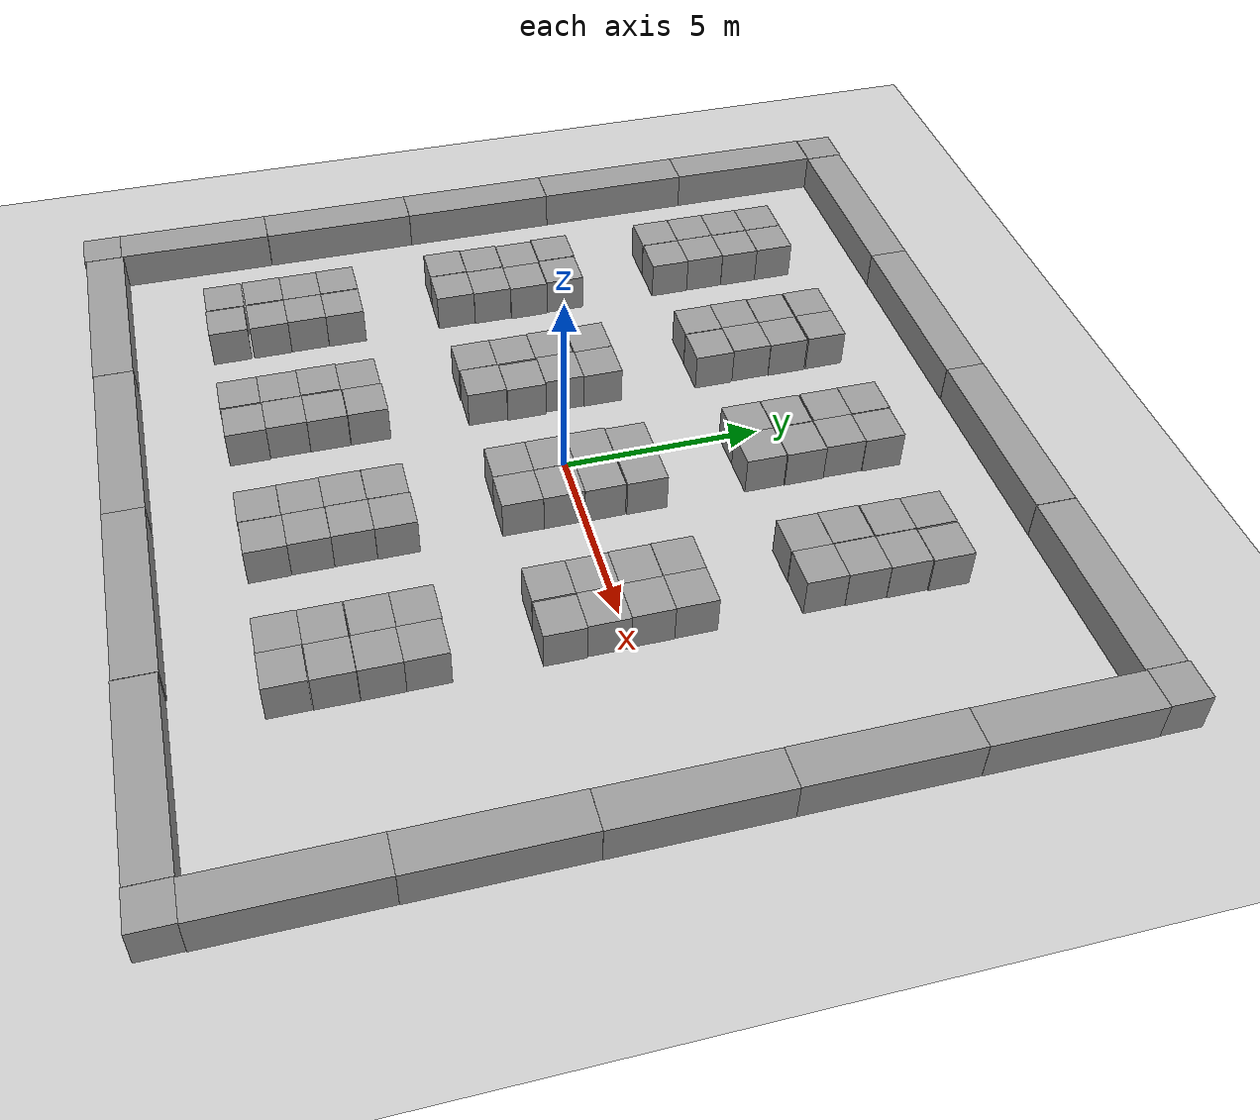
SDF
<sdf version="1.7">
 <world name="default">
  <light name="sun" type="directional">
   <pose>0 0 10 0 -0 0</pose>
   <diffuse>0.8 0.8 0.8 1</diffuse>
   <specular>0.2 0.2 0.2 1</specular>
   <attenuation>
    <range>1000</range>
    <constant>0.9</constant>
    <linear>0.01</linear>
    <quadratic>0.001</quadratic>
   </attenuation>
   <direction>-0.5 0.1 -0.9</direction>
   <spot><inner_angle>0</inner_angle><outer_angle>0</outer_angle><falloff>0</falloff></spot>
  </light>
  <model name="ground_plane">
   <static>1</static>
   <link name="link">
    <collision name="collision">
     <geometry><plane><normal>0 0 1</normal><size>100 100</size></plane></geometry>
     <surface>
      <contact><collide_bitmask>65535</collide_bitmask></contact>
      <friction><ode><mu>100</mu><mu2>50</mu2></ode></friction>
     </surface>
    </collision>
    <visual name="visual">
     <cast_shadows>0</cast_shadows>
     <geometry><plane><normal>0 0 1</normal><size>100 100</size></plane></geometry>
     <material>
      <script><uri>file://media/materials/scripts/gazebo.material</uri><name>Gazebo/Grey</name></script>
     </material>
    </visual>
   </link>
  </model>
  <gravity>0 0 -9.8</gravity>
  <magnetic_field>6e-06 2.3e-05 -4.2e-05</magnetic_field>
  <atmosphere type="adiabatic"/>
  <physics type="ode">
   <max_step_size>0.001</max_step_size>
   <real_time_factor>1</real_time_factor>
   <real_time_update_rate>1000</real_time_update_rate>
  </physics>
  <scene><ambient>0.4 0.4 0.4 1</ambient><background>0.7 0.7 0.7 1</background><shadows>1</shadows></scene>
  <audio><device>default</device></audio>
  <spherical_coordinates>
   <surface_model>EARTH_WGS84</surface_model>
   <latitude_deg>0</latitude_deg>
   <longitude_deg>0</longitude_deg>
   <elevation>0</elevation>
   <heading_deg>0</heading_deg>
  </spherical_coordinates>
  <model name="unit_box_3">
   <pose>-7.50361 7.53139 0.499995 0 1e-05 -5.5e-05</pose>
   <link name="link">
    <inertial>
     <mass>1</mass>
     <inertia>
      <ixx>0.166667</ixx>
      <ixy>0</ixy>
      <ixz>0</ixz>
      <iyy>0.166667</iyy>
      <iyz>0</iyz>
      <izz>0.166667</izz>
     </inertia>
    </inertial>
    <collision name="collision"><geometry><box><size>1 1 1</size></box></geometry></collision>
    <visual name="visual">
     <geometry><box><size>1 1 1</size></box></geometry>
     <material>
      <script><name>Gazebo/Grey</name><uri>file://media/materials/scripts/gazebo.material</uri></script>
     </material>
    </visual>
   </link>
  </model>
  <model name="unit_box_4">
   <pose>-6.49606 7.5287 0.499995 0 1e-05 0</pose>
   <link name="link">
    <inertial>
     <mass>1</mass>
     <inertia>
      <ixx>0.166667</ixx>
      <ixy>0</ixy>
      <ixz>0</ixz>
      <iyy>0.166667</iyy>
      <iyz>0</iyz>
      <izz>0.166667</izz>
     </inertia>
    </inertial>
    <collision name="collision"><geometry><box><size>1 1 1</size></box></geometry></collision>
    <visual name="visual">
     <geometry><box><size>1 1 1</size></box></geometry>
     <material>
      <script><name>Gazebo/Grey</name><uri>file://media/materials/scripts/gazebo.material</uri></script>
     </material>
    </visual>
   </link>
  </model>
  <model name="ball_bearing">
   <link name="link">
    <pose>0 0 0.003 0 -0 0</pose>
    <inertial>
     <mass>0.0011</mass>
     <inertia>
      <ixx>3.96e-09</ixx>
      <ixy>0</ixy>
      <ixz>0</ixz>
      <iyy>3.96e-09</iyy>
      <iyz>0</iyz>
      <izz>3.96e-09</izz>
     </inertia>
    </inertial>
    <collision name="collision">
     <geometry><sphere><radius>0.003</radius></sphere></geometry>
     <surface>
      <contact>
       <poissons_ratio>0.305</poissons_ratio>
       <elastic_modulus>2e+11</elastic_modulus>
       <ode><kp>100000</kp><kd>100</kd><max_vel>100</max_vel><min_depth>0.001</min_depth></ode>
      </contact>
      <friction>
       <torsional>
        <coefficient>1</coefficient>
        <use_patch_radius>0</use_patch_radius>
        <surface_radius>0.01</surface_radius>
       </torsional>
      </friction>
     </surface>
    </collision>
    <visual name="visual">
     <geometry><sphere><radius>0.003</radius></sphere></geometry>
     <material>
      <script><uri>file://media/materials/scripts/gazebo.material</uri><name>Gazebo/Grey</name></script>
     </material>
    </visual>
    <velocity_decay><linear>0</linear><angular>0.005</angular></velocity_decay>
   </link>
   <pose>-4.45266 -2.79694 -0.000369 0 -0 0</pose>
  </model>
  <model name="unit_box_5">
   <pose>-7.50463 6.53138 0.499995 -0 1e-05 -5.4e-05</pose>
   <link name="link">
    <inertial>
     <mass>1</mass>
     <inertia>
      <ixx>0.166667</ixx>
      <ixy>0</ixy>
      <ixz>0</ixz>
      <iyy>0.166667</iyy>
      <iyz>0</iyz>
      <izz>0.166667</izz>
     </inertia>
    </inertial>
    <collision name="collision"><geometry><box><size>1 1 1</size></box></geometry></collision>
    <visual name="visual">
     <geometry><box><size>1 1 1</size></box></geometry>
     <material>
      <script><name>Gazebo/Grey</name><uri>file://media/materials/scripts/gazebo.material</uri></script>
     </material>
    </visual>
   </link>
  </model>
  <model name="unit_box_7">
   <pose>-7.51098 5.53137 0.499995 0 -1e-05 -6.3e-05</pose>
   <link name="link">
    <inertial>
     <mass>1</mass>
     <inertia>
      <ixx>0.166667</ixx>
      <ixy>0</ixy>
      <ixz>0</ixz>
      <iyy>0.166667</iyy>
      <iyz>0</iyz>
      <izz>0.166667</izz>
     </inertia>
    </inertial>
    <collision name="collision"><geometry><box><size>1 1 1</size></box></geometry></collision>
    <visual name="visual">
     <geometry><box><size>1 1 1</size></box></geometry>
     <material>
      <script><name>Gazebo/Grey</name><uri>file://media/materials/scripts/gazebo.material</uri></script>
     </material>
    </visual>
   </link>
  </model>
  <model name="unit_box_8">
   <pose>-6.5049 5.5275 0.499995 -1e-05 -0 -0.000313</pose>
   <link name="link">
    <inertial>
     <mass>1</mass>
     <inertia>
      <ixx>0.166667</ixx>
      <ixy>0</ixy>
      <ixz>0</ixz>
      <iyy>0.166667</iyy>
      <iyz>0</iyz>
      <izz>0.166667</izz>
     </inertia>
    </inertial>
    <collision name="collision"><geometry><box><size>1 1 1</size></box></geometry></collision>
    <visual name="visual">
     <geometry><box><size>1 1 1</size></box></geometry>
     <material>
      <script><name>Gazebo/Grey</name><uri>file://media/materials/scripts/gazebo.material</uri></script>
     </material>
    </visual>
   </link>
  </model>
  <model name="unit_box_9">
   <pose>-7.50552 4.52464 0.499995 0 1e-05 0</pose>
   <link name="link">
    <inertial>
     <mass>1</mass>
     <inertia>
      <ixx>0.166667</ixx>
      <ixy>0</ixy>
      <ixz>0</ixz>
      <iyy>0.166667</iyy>
      <iyz>0</iyz>
      <izz>0.166667</izz>
     </inertia>
    </inertial>
    <collision name="collision"><geometry><box><size>1 1 1</size></box></geometry></collision>
    <visual name="visual">
     <geometry><box><size>1 1 1</size></box></geometry>
     <material>
      <script><name>Gazebo/Grey</name><uri>file://media/materials/scripts/gazebo.material</uri></script>
     </material>
    </visual>
   </link>
  </model>
  <model name="unit_box_10">
   <pose>-6.49293 4.52745 0.499995 -0 1e-05 -0.000247</pose>
   <link name="link">
    <inertial>
     <mass>1</mass>
     <inertia>
      <ixx>0.166667</ixx>
      <ixy>0</ixy>
      <ixz>0</ixz>
      <iyy>0.166667</iyy>
      <iyz>0</iyz>
      <izz>0.166667</izz>
     </inertia>
    </inertial>
    <collision name="collision"><geometry><box><size>1 1 1</size></box></geometry></collision>
    <visual name="visual">
     <geometry><box><size>1 1 1</size></box></geometry>
     <material>
      <script><name>Gazebo/Grey</name><uri>file://media/materials/scripts/gazebo.material</uri></script>
     </material>
    </visual>
   </link>
  </model>
  <model name="unit_box_6">
   <pose>-6.49182 6.52749 0.499995 0 1e-05 -0.000314</pose>
   <link name="link">
    <inertial>
     <mass>1</mass>
     <inertia>
      <ixx>0.166667</ixx>
      <ixy>0</ixy>
      <ixz>0</ixz>
      <iyy>0.166667</iyy>
      <iyz>0</iyz>
      <izz>0.166667</izz>
     </inertia>
    </inertial>
    <collision name="collision"><geometry><box><size>1 1 1</size></box></geometry></collision>
    <visual name="visual">
     <geometry><box><size>1 1 1</size></box></geometry>
     <material>
      <script><name>Gazebo/Grey</name><uri>file://media/materials/scripts/gazebo.material</uri></script>
     </material>
    </visual>
   </link>
  </model>
  <model name="unit_box_11">
   <pose>-3.49602 7.55128 0.499995 1e-05 -0 4.2e-05</pose>
   <link name="link">
    <inertial>
     <mass>1</mass>
     <inertia>
      <ixx>0.166667</ixx>
      <ixy>0</ixy>
      <ixz>0</ixz>
      <iyy>0.166667</iyy>
      <iyz>0</iyz>
      <izz>0.166667</izz>
     </inertia>
    </inertial>
    <collision name="collision"><geometry><box><size>1 1 1</size></box></geometry></collision>
    <visual name="visual">
     <geometry><box><size>1 1 1</size></box></geometry>
     <material>
      <script><name>Gazebo/Grey</name><uri>file://media/materials/scripts/gazebo.material</uri></script>
     </material>
    </visual>
   </link>
  </model>
  <model name="unit_box_12">
   <pose>-2.49602 7.55405 0.499995 -1e-05 -0 4.2e-05</pose>
   <link name="link">
    <inertial>
     <mass>1</mass>
     <inertia>
      <ixx>0.166667</ixx>
      <ixy>0</ixy>
      <ixz>0</ixz>
      <iyy>0.166667</iyy>
      <iyz>0</iyz>
      <izz>0.166667</izz>
     </inertia>
    </inertial>
    <collision name="collision"><geometry><box><size>1 1 1</size></box></geometry></collision>
    <visual name="visual">
     <geometry><box><size>1 1 1</size></box></geometry>
     <material>
      <script><name>Gazebo/Grey</name><uri>file://media/materials/scripts/gazebo.material</uri></script>
     </material>
    </visual>
   </link>
  </model>
  <model name="unit_box_13">
   <pose>-3.48434 6.51776 0.499995 1e-05 -0 0.000317</pose>
   <link name="link">
    <inertial>
     <mass>1</mass>
     <inertia>
      <ixx>0.166667</ixx>
      <ixy>0</ixy>
      <ixz>0</ixz>
      <iyy>0.166667</iyy>
      <iyz>0</iyz>
      <izz>0.166667</izz>
     </inertia>
    </inertial>
    <collision name="collision"><geometry><box><size>1 1 1</size></box></geometry></collision>
    <visual name="visual">
     <geometry><box><size>1 1 1</size></box></geometry>
     <material>
      <script><name>Gazebo/Grey</name><uri>file://media/materials/scripts/gazebo.material</uri></script>
     </material>
    </visual>
   </link>
  </model>
  <model name="unit_box_14">
   <pose>-2.48433 6.51289 0.5 0 -0 0.000316</pose>
   <link name="link">
    <inertial>
     <mass>1</mass>
     <inertia>
      <ixx>0.166667</ixx>
      <ixy>0</ixy>
      <ixz>0</ixz>
      <iyy>0.166667</iyy>
      <iyz>0</iyz>
      <izz>0.166667</izz>
     </inertia>
    </inertial>
    <collision name="collision"><geometry><box><size>1 1 1</size></box></geometry></collision>
    <visual name="visual">
     <geometry><box><size>1 1 1</size></box></geometry>
     <material>
      <script><name>Gazebo/Grey</name><uri>file://media/materials/scripts/gazebo.material</uri></script>
     </material>
    </visual>
   </link>
  </model>
  <model name="unit_box_15">
   <pose>-3.50144 5.50839 0.499995 -0 -1e-05 0.000289</pose>
   <link name="link">
    <inertial>
     <mass>1</mass>
     <inertia>
      <ixx>0.166667</ixx>
      <ixy>0</ixy>
      <ixz>0</ixz>
      <iyy>0.166667</iyy>
      <iyz>0</iyz>
      <izz>0.166667</izz>
     </inertia>
    </inertial>
    <collision name="collision"><geometry><box><size>1 1 1</size></box></geometry></collision>
    <visual name="visual">
     <geometry><box><size>1 1 1</size></box></geometry>
     <material>
      <script><name>Gazebo/Grey</name><uri>file://media/materials/scripts/gazebo.material</uri></script>
     </material>
    </visual>
   </link>
  </model>
  <model name="unit_box_16">
   <pose>-2.50142 5.51286 0.499995 1e-05 -0 0.000288</pose>
   <link name="link">
    <inertial>
     <mass>1</mass>
     <inertia>
      <ixx>0.166667</ixx>
      <ixy>0</ixy>
      <ixz>0</ixz>
      <iyy>0.166667</iyy>
      <iyz>0</iyz>
      <izz>0.166667</izz>
     </inertia>
    </inertial>
    <collision name="collision"><geometry><box><size>1 1 1</size></box></geometry></collision>
    <visual name="visual">
     <geometry><box><size>1 1 1</size></box></geometry>
     <material>
      <script><name>Gazebo/Grey</name><uri>file://media/materials/scripts/gazebo.material</uri></script>
     </material>
    </visual>
   </link>
  </model>
  <model name="unit_box_17">
   <pose>-3.48682 4.50839 0.499995 0 -1e-05 0.00029</pose>
   <link name="link">
    <inertial>
     <mass>1</mass>
     <inertia>
      <ixx>0.166667</ixx>
      <ixy>0</ixy>
      <ixz>0</ixz>
      <iyy>0.166667</iyy>
      <iyz>0</iyz>
      <izz>0.166667</izz>
     </inertia>
    </inertial>
    <collision name="collision"><geometry><box><size>1 1 1</size></box></geometry></collision>
    <visual name="visual">
     <geometry><box><size>1 1 1</size></box></geometry>
     <material>
      <script><name>Gazebo/Grey</name><uri>file://media/materials/scripts/gazebo.material</uri></script>
     </material>
    </visual>
   </link>
  </model>
  <model name="unit_box_18">
   <pose>-2.46798 4.50679 0.499995 0 1e-05 0</pose>
   <link name="link">
    <inertial>
     <mass>1</mass>
     <inertia>
      <ixx>0.166667</ixx>
      <ixy>0</ixy>
      <ixz>0</ixz>
      <iyy>0.166667</iyy>
      <iyz>0</iyz>
      <izz>0.166667</izz>
     </inertia>
    </inertial>
    <collision name="collision"><geometry><box><size>1 1 1</size></box></geometry></collision>
    <visual name="visual">
     <geometry><box><size>1 1 1</size></box></geometry>
     <material>
      <script><name>Gazebo/Grey</name><uri>file://media/materials/scripts/gazebo.material</uri></script>
     </material>
    </visual>
   </link>
  </model>
  <model name="unit_box_19">
   <pose>0.486806 7.5569 0.499995 0 1e-05 -0.003814</pose>
   <link name="link">
    <inertial>
     <mass>1</mass>
     <inertia>
      <ixx>0.166667</ixx>
      <ixy>0</ixy>
      <ixz>0</ixz>
      <iyy>0.166667</iyy>
      <iyz>0</iyz>
      <izz>0.166667</izz>
     </inertia>
    </inertial>
    <collision name="collision"><geometry><box><size>1 1 1</size></box></geometry></collision>
    <visual name="visual">
     <geometry><box><size>1 1 1</size></box></geometry>
     <material>
      <script><name>Gazebo/Grey</name><uri>file://media/materials/scripts/gazebo.material</uri></script>
     </material>
    </visual>
   </link>
  </model>
  <model name="unit_box_20">
   <pose>0.484165 6.55672 0.499995 -1e-05 0 -0.003555</pose>
   <link name="link">
    <inertial>
     <mass>1</mass>
     <inertia>
      <ixx>0.166667</ixx>
      <ixy>0</ixy>
      <ixz>0</ixz>
      <iyy>0.166667</iyy>
      <iyz>0</iyz>
      <izz>0.166667</izz>
     </inertia>
    </inertial>
    <collision name="collision"><geometry><box><size>1 1 1</size></box></geometry></collision>
    <visual name="visual">
     <geometry><box><size>1 1 1</size></box></geometry>
     <material>
      <script><name>Gazebo/Grey</name><uri>file://media/materials/scripts/gazebo.material</uri></script>
     </material>
    </visual>
   </link>
  </model>
  <model name="unit_box_21">
   <pose>1.50946 7.53476 0.499995 1e-05 -0 -0.003222</pose>
   <link name="link">
    <inertial>
     <mass>1</mass>
     <inertia>
      <ixx>0.166667</ixx>
      <ixy>0</ixy>
      <ixz>0</ixz>
      <iyy>0.166667</iyy>
      <iyz>0</iyz>
      <izz>0.166667</izz>
     </inertia>
    </inertial>
    <collision name="collision"><geometry><box><size>1 1 1</size></box></geometry></collision>
    <visual name="visual">
     <geometry><box><size>1 1 1</size></box></geometry>
     <material>
      <script><name>Gazebo/Grey</name><uri>file://media/materials/scripts/gazebo.material</uri></script>
     </material>
    </visual>
   </link>
  </model>
  <model name="unit_box_22">
   <pose>1.48426 6.5347 0.499995 1e-05 -0 -0.003346</pose>
   <link name="link">
    <inertial>
     <mass>1</mass>
     <inertia>
      <ixx>0.166667</ixx>
      <ixy>0</ixy>
      <ixz>0</ixz>
      <iyy>0.166667</iyy>
      <iyz>0</iyz>
      <izz>0.166667</izz>
     </inertia>
    </inertial>
    <collision name="collision"><geometry><box><size>1 1 1</size></box></geometry></collision>
    <visual name="visual">
     <geometry><box><size>1 1 1</size></box></geometry>
     <material>
      <script><name>Gazebo/Grey</name><uri>file://media/materials/scripts/gazebo.material</uri></script>
     </material>
    </visual>
   </link>
  </model>
  <model name="unit_box_23">
   <pose>0.491891 5.52017 0.499995 0 1e-05 0</pose>
   <link name="link">
    <inertial>
     <mass>1</mass>
     <inertia>
      <ixx>0.166667</ixx>
      <ixy>0</ixy>
      <ixz>0</ixz>
      <iyy>0.166667</iyy>
      <iyz>0</iyz>
      <izz>0.166667</izz>
     </inertia>
    </inertial>
    <collision name="collision"><geometry><box><size>1 1 1</size></box></geometry></collision>
    <visual name="visual">
     <geometry><box><size>1 1 1</size></box></geometry>
     <material>
      <script><name>Gazebo/Grey</name><uri>file://media/materials/scripts/gazebo.material</uri></script>
     </material>
    </visual>
   </link>
  </model>
  <model name="unit_box_24">
   <pose>1.50944 5.52411 0.499995 0 1e-05 0</pose>
   <link name="link">
    <inertial>
     <mass>1</mass>
     <inertia>
      <ixx>0.166667</ixx>
      <ixy>0</ixy>
      <ixz>0</ixz>
      <iyy>0.166667</iyy>
      <iyz>0</iyz>
      <izz>0.166667</izz>
     </inertia>
    </inertial>
    <collision name="collision"><geometry><box><size>1 1 1</size></box></geometry></collision>
    <visual name="visual">
     <geometry><box><size>1 1 1</size></box></geometry>
     <material>
      <script><name>Gazebo/Grey</name><uri>file://media/materials/scripts/gazebo.material</uri></script>
     </material>
    </visual>
   </link>
  </model>
  <model name="unit_box_25">
   <pose>0.492022 4.50931 0.499995 1e-05 -0 5e-06</pose>
   <link name="link">
    <inertial>
     <mass>1</mass>
     <inertia>
      <ixx>0.166667</ixx>
      <ixy>0</ixy>
      <ixz>0</ixz>
      <iyy>0.166667</iyy>
      <iyz>0</iyz>
      <izz>0.166667</izz>
     </inertia>
    </inertial>
    <collision name="collision"><geometry><box><size>1 1 1</size></box></geometry></collision>
    <visual name="visual">
     <geometry><box><size>1 1 1</size></box></geometry>
     <material>
      <script><name>Gazebo/Grey</name><uri>file://media/materials/scripts/gazebo.material</uri></script>
     </material>
    </visual>
   </link>
  </model>
  <model name="unit_box_26">
   <pose>1.49204 4.50876 0.499995 -1e-05 -0 1e-05</pose>
   <link name="link">
    <inertial>
     <mass>1</mass>
     <inertia>
      <ixx>0.166667</ixx>
      <ixy>0</ixy>
      <ixz>0</ixz>
      <iyy>0.166667</iyy>
      <iyz>0</iyz>
      <izz>0.166667</izz>
     </inertia>
    </inertial>
    <collision name="collision"><geometry><box><size>1 1 1</size></box></geometry></collision>
    <visual name="visual">
     <geometry><box><size>1 1 1</size></box></geometry>
     <material>
      <script><name>Gazebo/Grey</name><uri>file://media/materials/scripts/gazebo.material</uri></script>
     </material>
    </visual>
   </link>
  </model>
  <model name="unit_box_27">
   <pose>4.51157 7.53417 0.499995 -1e-05 -0 -2.4e-05</pose>
   <link name="link">
    <inertial>
     <mass>1</mass>
     <inertia>
      <ixx>0.166667</ixx>
      <ixy>0</ixy>
      <ixz>0</ixz>
      <iyy>0.166667</iyy>
      <iyz>0</iyz>
      <izz>0.166667</izz>
     </inertia>
    </inertial>
    <collision name="collision"><geometry><box><size>1 1 1</size></box></geometry></collision>
    <visual name="visual">
     <geometry><box><size>1 1 1</size></box></geometry>
     <material>
      <script><name>Gazebo/Grey</name><uri>file://media/materials/scripts/gazebo.material</uri></script>
     </material>
    </visual>
   </link>
  </model>
  <model name="unit_box_28">
   <pose>5.55239 7.52483 0.499995 0 1e-05 0</pose>
   <link name="link">
    <inertial>
     <mass>1</mass>
     <inertia>
      <ixx>0.166667</ixx>
      <ixy>0</ixy>
      <ixz>0</ixz>
      <iyy>0.166667</iyy>
      <iyz>0</iyz>
      <izz>0.166667</izz>
     </inertia>
    </inertial>
    <collision name="collision"><geometry><box><size>1 1 1</size></box></geometry></collision>
    <visual name="visual">
     <geometry><box><size>1 1 1</size></box></geometry>
     <material>
      <script><name>Gazebo/Grey</name><uri>file://media/materials/scripts/gazebo.material</uri></script>
     </material>
    </visual>
   </link>
  </model>
  <model name="unit_box_29">
   <pose>4.50242 6.53416 0.499995 0 1e-05 -2.3e-05</pose>
   <link name="link">
    <inertial>
     <mass>1</mass>
     <inertia>
      <ixx>0.166667</ixx>
      <ixy>0</ixy>
      <ixz>0</ixz>
      <iyy>0.166667</iyy>
      <iyz>0</iyz>
      <izz>0.166667</izz>
     </inertia>
    </inertial>
    <collision name="collision"><geometry><box><size>1 1 1</size></box></geometry></collision>
    <visual name="visual">
     <geometry><box><size>1 1 1</size></box></geometry>
     <material>
      <script><name>Gazebo/Grey</name><uri>file://media/materials/scripts/gazebo.material</uri></script>
     </material>
    </visual>
   </link>
  </model>
  <model name="unit_box_30">
   <pose>5.51848 6.5195 0.499995 0 1e-05 7.5e-05</pose>
   <link name="link">
    <inertial>
     <mass>1</mass>
     <inertia>
      <ixx>0.166667</ixx>
      <ixy>0</ixy>
      <ixz>0</ixz>
      <iyy>0.166667</iyy>
      <iyz>0</iyz>
      <izz>0.166667</izz>
     </inertia>
    </inertial>
    <collision name="collision"><geometry><box><size>1 1 1</size></box></geometry></collision>
    <visual name="visual">
     <geometry><box><size>1 1 1</size></box></geometry>
     <material>
      <script><name>Gazebo/Grey</name><uri>file://media/materials/scripts/gazebo.material</uri></script>
     </material>
    </visual>
   </link>
  </model>
  <model name="unit_box_31">
   <pose>4.48757 5.5114 0.499995 0 1e-05 0</pose>
   <link name="link">
    <inertial>
     <mass>1</mass>
     <inertia>
      <ixx>0.166667</ixx>
      <ixy>0</ixy>
      <ixz>0</ixz>
      <iyy>0.166667</iyy>
      <iyz>0</iyz>
      <izz>0.166667</izz>
     </inertia>
    </inertial>
    <collision name="collision"><geometry><box><size>1 1 1</size></box></geometry></collision>
    <visual name="visual">
     <geometry><box><size>1 1 1</size></box></geometry>
     <material>
      <script><name>Gazebo/Grey</name><uri>file://media/materials/scripts/gazebo.material</uri></script>
     </material>
    </visual>
   </link>
  </model>
  <model name="unit_box_32">
   <pose>5.50629 5.51942 0.499995 -1e-05 -0 4.7e-05</pose>
   <link name="link">
    <inertial>
     <mass>1</mass>
     <inertia>
      <ixx>0.166667</ixx>
      <ixy>0</ixy>
      <ixz>0</ixz>
      <iyy>0.166667</iyy>
      <iyz>0</iyz>
      <izz>0.166667</izz>
     </inertia>
    </inertial>
    <collision name="collision"><geometry><box><size>1 1 1</size></box></geometry></collision>
    <visual name="visual">
     <geometry><box><size>1 1 1</size></box></geometry>
     <material>
      <script><name>Gazebo/Grey</name><uri>file://media/materials/scripts/gazebo.material</uri></script>
     </material>
    </visual>
   </link>
  </model>
  <model name="unit_box_33">
   <pose>4.49774 4.5066 0.499995 1e-05 0 -0.000363</pose>
   <link name="link">
    <inertial>
     <mass>1</mass>
     <inertia>
      <ixx>0.166667</ixx>
      <ixy>0</ixy>
      <ixz>0</ixz>
      <iyy>0.166667</iyy>
      <iyz>0</iyz>
      <izz>0.166667</izz>
     </inertia>
    </inertial>
    <collision name="collision"><geometry><box><size>1 1 1</size></box></geometry></collision>
    <visual name="visual">
     <geometry><box><size>1 1 1</size></box></geometry>
     <material>
      <script><name>Gazebo/Grey</name><uri>file://media/materials/scripts/gazebo.material</uri></script>
     </material>
    </visual>
   </link>
  </model>
  <model name="unit_box_34">
   <pose>5.49784 4.51923 0.499995 -1e-05 -0 -0.000195</pose>
   <link name="link">
    <inertial>
     <mass>1</mass>
     <inertia>
      <ixx>0.166667</ixx>
      <ixy>0</ixy>
      <ixz>0</ixz>
      <iyy>0.166667</iyy>
      <iyz>0</iyz>
      <izz>0.166667</izz>
     </inertia>
    </inertial>
    <collision name="collision"><geometry><box><size>1 1 1</size></box></geometry></collision>
    <visual name="visual">
     <geometry><box><size>1 1 1</size></box></geometry>
     <material>
      <script><name>Gazebo/Grey</name><uri>file://media/materials/scripts/gazebo.material</uri></script>
     </material>
    </visual>
   </link>
  </model>
  <model name="unit_box_35">
   <pose>-7.51114 1.54685 0.499995 0 1e-05 0</pose>
   <link name="link">
    <inertial>
     <mass>1</mass>
     <inertia>
      <ixx>0.166667</ixx>
      <ixy>0</ixy>
      <ixz>0</ixz>
      <iyy>0.166667</iyy>
      <iyz>0</iyz>
      <izz>0.166667</izz>
     </inertia>
    </inertial>
    <collision name="collision"><geometry><box><size>1 1 1</size></box></geometry></collision>
    <visual name="visual">
     <geometry><box><size>1 1 1</size></box></geometry>
     <material>
      <script><name>Gazebo/Grey</name><uri>file://media/materials/scripts/gazebo.material</uri></script>
     </material>
    </visual>
   </link>
  </model>
  <model name="unit_box_36">
   <pose>-6.4947 1.53041 0.499995 0 1e-05 0</pose>
   <link name="link">
    <inertial>
     <mass>1</mass>
     <inertia>
      <ixx>0.166667</ixx>
      <ixy>0</ixy>
      <ixz>0</ixz>
      <iyy>0.166667</iyy>
      <iyz>0</iyz>
      <izz>0.166667</izz>
     </inertia>
    </inertial>
    <collision name="collision"><geometry><box><size>1 1 1</size></box></geometry></collision>
    <visual name="visual">
     <geometry><box><size>1 1 1</size></box></geometry>
     <material>
      <script><name>Gazebo/Grey</name><uri>file://media/materials/scripts/gazebo.material</uri></script>
     </material>
    </visual>
   </link>
  </model>
  <model name="unit_box_37">
   <pose>-7.45951 0.528875 0.499995 -0 1e-05 -0.001052</pose>
   <link name="link">
    <inertial>
     <mass>1</mass>
     <inertia>
      <ixx>0.166667</ixx>
      <ixy>0</ixy>
      <ixz>0</ixz>
      <iyy>0.166667</iyy>
      <iyz>0</iyz>
      <izz>0.166667</izz>
     </inertia>
    </inertial>
    <collision name="collision"><geometry><box><size>1 1 1</size></box></geometry></collision>
    <visual name="visual">
     <geometry><box><size>1 1 1</size></box></geometry>
     <material>
      <script><name>Gazebo/Grey</name><uri>file://media/materials/scripts/gazebo.material</uri></script>
     </material>
    </visual>
   </link>
  </model>
  <model name="unit_box_38">
   <pose>-6.45898 0.514165 0.499995 -1e-05 -0 -0.00116</pose>
   <link name="link">
    <inertial>
     <mass>1</mass>
     <inertia>
      <ixx>0.166667</ixx>
      <ixy>0</ixy>
      <ixz>0</ixz>
      <iyy>0.166667</iyy>
      <iyz>0</iyz>
      <izz>0.166667</izz>
     </inertia>
    </inertial>
    <collision name="collision"><geometry><box><size>1 1 1</size></box></geometry></collision>
    <visual name="visual">
     <geometry><box><size>1 1 1</size></box></geometry>
     <material>
      <script><name>Gazebo/Grey</name><uri>file://media/materials/scripts/gazebo.material</uri></script>
     </material>
    </visual>
   </link>
  </model>
  <model name="unit_box_39">
   <pose>-7.50251 -0.477823 0.499995 0 1e-05 0</pose>
   <link name="link">
    <inertial>
     <mass>1</mass>
     <inertia>
      <ixx>0.166667</ixx>
      <ixy>0</ixy>
      <ixz>0</ixz>
      <iyy>0.166667</iyy>
      <iyz>0</iyz>
      <izz>0.166667</izz>
     </inertia>
    </inertial>
    <collision name="collision"><geometry><box><size>1 1 1</size></box></geometry></collision>
    <visual name="visual">
     <geometry><box><size>1 1 1</size></box></geometry>
     <material>
      <script><name>Gazebo/Grey</name><uri>file://media/materials/scripts/gazebo.material</uri></script>
     </material>
    </visual>
   </link>
  </model>
  <model name="unit_box_40">
   <pose>-6.49573 -0.485833 0.499995 1e-05 0 -0.001146</pose>
   <link name="link">
    <inertial>
     <mass>1</mass>
     <inertia>
      <ixx>0.166667</ixx>
      <ixy>0</ixy>
      <ixz>0</ixz>
      <iyy>0.166667</iyy>
      <iyz>0</iyz>
      <izz>0.166667</izz>
     </inertia>
    </inertial>
    <collision name="collision"><geometry><box><size>1 1 1</size></box></geometry></collision>
    <visual name="visual">
     <geometry><box><size>1 1 1</size></box></geometry>
     <material>
      <script><name>Gazebo/Grey</name><uri>file://media/materials/scripts/gazebo.material</uri></script>
     </material>
    </visual>
   </link>
  </model>
  <model name="unit_box_41">
   <pose>-7.53449 -1.48259 0.499995 0 1e-05 0</pose>
   <link name="link">
    <inertial>
     <mass>1</mass>
     <inertia>
      <ixx>0.166667</ixx>
      <ixy>0</ixy>
      <ixz>0</ixz>
      <iyy>0.166667</iyy>
      <iyz>0</iyz>
      <izz>0.166667</izz>
     </inertia>
    </inertial>
    <collision name="collision"><geometry><box><size>1 1 1</size></box></geometry></collision>
    <visual name="visual">
     <geometry><box><size>1 1 1</size></box></geometry>
     <material>
      <script><name>Gazebo/Grey</name><uri>file://media/materials/scripts/gazebo.material</uri></script>
     </material>
    </visual>
   </link>
  </model>
  <model name="unit_box_42">
   <pose>-6.52039 -1.4858 0.499995 -1e-05 -0 -0.001146</pose>
   <link name="link">
    <inertial>
     <mass>1</mass>
     <inertia>
      <ixx>0.166667</ixx>
      <ixy>0</ixy>
      <ixz>0</ixz>
      <iyy>0.166667</iyy>
      <iyz>0</iyz>
      <izz>0.166667</izz>
     </inertia>
    </inertial>
    <collision name="collision"><geometry><box><size>1 1 1</size></box></geometry></collision>
    <visual name="visual">
     <geometry><box><size>1 1 1</size></box></geometry>
     <material>
      <script><name>Gazebo/Grey</name><uri>file://media/materials/scripts/gazebo.material</uri></script>
     </material>
    </visual>
   </link>
  </model>
  <model name="unit_box_43">
   <pose>-3.49211 1.51005 0.499995 -1e-05 -0 0.008286</pose>
   <link name="link">
    <inertial>
     <mass>1</mass>
     <inertia>
      <ixx>0.166667</ixx>
      <ixy>0</ixy>
      <ixz>0</ixz>
      <iyy>0.166667</iyy>
      <iyz>0</iyz>
      <izz>0.166667</izz>
     </inertia>
    </inertial>
    <collision name="collision"><geometry><box><size>1 1 1</size></box></geometry></collision>
    <visual name="visual">
     <geometry><box><size>1 1 1</size></box></geometry>
     <material>
      <script><name>Gazebo/Grey</name><uri>file://media/materials/scripts/gazebo.material</uri></script>
     </material>
    </visual>
   </link>
  </model>
  <model name="unit_box_44">
   <pose>-2.48883 1.51534 0.499995 1e-05 -0 0.001695</pose>
   <link name="link">
    <inertial>
     <mass>1</mass>
     <inertia>
      <ixx>0.166667</ixx>
      <ixy>0</ixy>
      <ixz>0</ixz>
      <iyy>0.166667</iyy>
      <iyz>0</iyz>
      <izz>0.166667</izz>
     </inertia>
    </inertial>
    <collision name="collision"><geometry><box><size>1 1 1</size></box></geometry></collision>
    <visual name="visual">
     <geometry><box><size>1 1 1</size></box></geometry>
     <material>
      <script><name>Gazebo/Grey</name><uri>file://media/materials/scripts/gazebo.material</uri></script>
     </material>
    </visual>
   </link>
  </model>
  <model name="unit_box_45">
   <pose>-3.51074 0.487476 0.5 0 -0 0.002136</pose>
   <link name="link">
    <inertial>
     <mass>1</mass>
     <inertia>
      <ixx>0.166667</ixx>
      <ixy>0</ixy>
      <ixz>0</ixz>
      <iyy>0.166667</iyy>
      <iyz>0</iyz>
      <izz>0.166667</izz>
     </inertia>
    </inertial>
    <collision name="collision"><geometry><box><size>1 1 1</size></box></geometry></collision>
    <visual name="visual">
     <geometry><box><size>1 1 1</size></box></geometry>
     <material>
      <script><name>Gazebo/Grey</name><uri>file://media/materials/scripts/gazebo.material</uri></script>
     </material>
    </visual>
   </link>
  </model>
  <model name="unit_box_46">
   <pose>-2.51002 0.514275 0.500001 -1e-06 -0 0.000579</pose>
   <link name="link">
    <inertial>
     <mass>1</mass>
     <inertia>
      <ixx>0.166667</ixx>
      <ixy>0</ixy>
      <ixz>0</ixz>
      <iyy>0.166667</iyy>
      <iyz>0</iyz>
      <izz>0.166667</izz>
     </inertia>
    </inertial>
    <collision name="collision"><geometry><box><size>1 1 1</size></box></geometry></collision>
    <visual name="visual">
     <geometry><box><size>1 1 1</size></box></geometry>
     <material>
      <script><name>Gazebo/Grey</name><uri>file://media/materials/scripts/gazebo.material</uri></script>
     </material>
    </visual>
   </link>
  </model>
  <model name="unit_box_47">
   <pose>-3.48688 -0.512956 0.5 0 -0 0.003058</pose>
   <link name="link">
    <inertial>
     <mass>1</mass>
     <inertia>
      <ixx>0.166667</ixx>
      <ixy>0</ixy>
      <ixz>0</ixz>
      <iyy>0.166667</iyy>
      <iyz>0</iyz>
      <izz>0.166667</izz>
     </inertia>
    </inertial>
    <collision name="collision"><geometry><box><size>1 1 1</size></box></geometry></collision>
    <visual name="visual">
     <geometry><box><size>1 1 1</size></box></geometry>
     <material>
      <script><name>Gazebo/Grey</name><uri>file://media/materials/scripts/gazebo.material</uri></script>
     </material>
    </visual>
   </link>
  </model>
  <model name="unit_box_48">
   <pose>-2.43745 -0.487554 0.499995 1e-05 -0 -0.003008</pose>
   <link name="link">
    <inertial>
     <mass>1</mass>
     <inertia>
      <ixx>0.166667</ixx>
      <ixy>0</ixy>
      <ixz>0</ixz>
      <iyy>0.166667</iyy>
      <iyz>0</iyz>
      <izz>0.166667</izz>
     </inertia>
    </inertial>
    <collision name="collision"><geometry><box><size>1 1 1</size></box></geometry></collision>
    <visual name="visual">
     <geometry><box><size>1 1 1</size></box></geometry>
     <material>
      <script><name>Gazebo/Grey</name><uri>file://media/materials/scripts/gazebo.material</uri></script>
     </material>
    </visual>
   </link>
  </model>
  <model name="unit_box_49">
   <pose>-3.49442 -1.51313 0.499995 1e-05 -0 0.003337</pose>
   <link name="link">
    <inertial>
     <mass>1</mass>
     <inertia>
      <ixx>0.166667</ixx>
      <ixy>0</ixy>
      <ixz>0</ixz>
      <iyy>0.166667</iyy>
      <iyz>0</iyz>
      <izz>0.166667</izz>
     </inertia>
    </inertial>
    <collision name="collision"><geometry><box><size>1 1 1</size></box></geometry></collision>
    <visual name="visual">
     <geometry><box><size>1 1 1</size></box></geometry>
     <material>
      <script><name>Gazebo/Grey</name><uri>file://media/materials/scripts/gazebo.material</uri></script>
     </material>
    </visual>
   </link>
  </model>
  <model name="unit_box_50">
   <pose>-2.48725 -1.48789 0.499995 0 -1e-05 -0.004023</pose>
   <link name="link">
    <inertial>
     <mass>1</mass>
     <inertia>
      <ixx>0.166667</ixx>
      <ixy>0</ixy>
      <ixz>0</ixz>
      <iyy>0.166667</iyy>
      <iyz>0</iyz>
      <izz>0.166667</izz>
     </inertia>
    </inertial>
    <collision name="collision"><geometry><box><size>1 1 1</size></box></geometry></collision>
    <visual name="visual">
     <geometry><box><size>1 1 1</size></box></geometry>
     <material>
      <script><name>Gazebo/Grey</name><uri>file://media/materials/scripts/gazebo.material</uri></script>
     </material>
    </visual>
   </link>
  </model>
  <model name="unit_box_51">
   <pose>0.526269 1.50642 0.499995 1e-05 -0 0.000133</pose>
   <link name="link">
    <inertial>
     <mass>1</mass>
     <inertia>
      <ixx>0.166667</ixx>
      <ixy>0</ixy>
      <ixz>0</ixz>
      <iyy>0.166667</iyy>
      <iyz>0</iyz>
      <izz>0.166667</izz>
     </inertia>
    </inertial>
    <collision name="collision"><geometry><box><size>1 1 1</size></box></geometry></collision>
    <visual name="visual">
     <geometry><box><size>1 1 1</size></box></geometry>
     <material>
      <script><name>Gazebo/Grey</name><uri>file://media/materials/scripts/gazebo.material</uri></script>
     </material>
    </visual>
   </link>
  </model>
  <model name="unit_box_52">
   <pose>1.52627 1.52478 0.499995 1e-05 -0 0.000136</pose>
   <link name="link">
    <inertial>
     <mass>1</mass>
     <inertia>
      <ixx>0.166667</ixx>
      <ixy>0</ixy>
      <ixz>0</ixz>
      <iyy>0.166667</iyy>
      <iyz>0</iyz>
      <izz>0.166667</izz>
     </inertia>
    </inertial>
    <collision name="collision"><geometry><box><size>1 1 1</size></box></geometry></collision>
    <visual name="visual">
     <geometry><box><size>1 1 1</size></box></geometry>
     <material>
      <script><name>Gazebo/Grey</name><uri>file://media/materials/scripts/gazebo.material</uri></script>
     </material>
    </visual>
   </link>
  </model>
  <model name="unit_box_53">
   <pose>0.474171 0.503729 0.499995 -1e-05 0 0.000364</pose>
   <link name="link">
    <inertial>
     <mass>1</mass>
     <inertia>
      <ixx>0.166667</ixx>
      <ixy>0</ixy>
      <ixz>0</ixz>
      <iyy>0.166667</iyy>
      <iyz>0</iyz>
      <izz>0.166667</izz>
     </inertia>
    </inertial>
    <collision name="collision"><geometry><box><size>1 1 1</size></box></geometry></collision>
    <visual name="visual">
     <geometry><box><size>1 1 1</size></box></geometry>
     <material>
      <script><name>Gazebo/Grey</name><uri>file://media/materials/scripts/gazebo.material</uri></script>
     </material>
    </visual>
   </link>
  </model>
  <model name="unit_box_54">
   <pose>1.51321 0.495733 0.499995 -1e-05 -0 0.002147</pose>
   <link name="link">
    <inertial>
     <mass>1</mass>
     <inertia>
      <ixx>0.166667</ixx>
      <ixy>0</ixy>
      <ixz>0</ixz>
      <iyy>0.166667</iyy>
      <iyz>0</iyz>
      <izz>0.166667</izz>
     </inertia>
    </inertial>
    <collision name="collision"><geometry><box><size>1 1 1</size></box></geometry></collision>
    <visual name="visual">
     <geometry><box><size>1 1 1</size></box></geometry>
     <material>
      <script><name>Gazebo/Grey</name><uri>file://media/materials/scripts/gazebo.material</uri></script>
     </material>
    </visual>
   </link>
  </model>
  <model name="unit_box_55">
   <pose>0.500287 -0.496286 0.5 0 -0 0.000333</pose>
   <link name="link">
    <inertial>
     <mass>1</mass>
     <inertia>
      <ixx>0.166667</ixx>
      <ixy>0</ixy>
      <ixz>0</ixz>
      <iyy>0.166667</iyy>
      <iyz>0</iyz>
      <izz>0.166667</izz>
     </inertia>
    </inertial>
    <collision name="collision"><geometry><box><size>1 1 1</size></box></geometry></collision>
    <visual name="visual">
     <geometry><box><size>1 1 1</size></box></geometry>
     <material>
      <script><name>Gazebo/Grey</name><uri>file://media/materials/scripts/gazebo.material</uri></script>
     </material>
    </visual>
   </link>
  </model>
  <model name="unit_box_56">
   <pose>1.50356 -0.504387 0.499995 0 -1e-05 0.002161</pose>
   <link name="link">
    <inertial>
     <mass>1</mass>
     <inertia>
      <ixx>0.166667</ixx>
      <ixy>0</ixy>
      <ixz>0</ixz>
      <iyy>0.166667</iyy>
      <iyz>0</iyz>
      <izz>0.166667</izz>
     </inertia>
    </inertial>
    <collision name="collision"><geometry><box><size>1 1 1</size></box></geometry></collision>
    <visual name="visual">
     <geometry><box><size>1 1 1</size></box></geometry>
     <material>
      <script><name>Gazebo/Grey</name><uri>file://media/materials/scripts/gazebo.material</uri></script>
     </material>
    </visual>
   </link>
  </model>
  <model name="unit_box_57">
   <pose>0.502014 -1.49634 0.499995 -1e-05 -0 0.000237</pose>
   <link name="link">
    <inertial>
     <mass>1</mass>
     <inertia>
      <ixx>0.166667</ixx>
      <ixy>0</ixy>
      <ixz>0</ixz>
      <iyy>0.166667</iyy>
      <iyz>0</iyz>
      <izz>0.166667</izz>
     </inertia>
    </inertial>
    <collision name="collision"><geometry><box><size>1 1 1</size></box></geometry></collision>
    <visual name="visual">
     <geometry><box><size>1 1 1</size></box></geometry>
     <material>
      <script><name>Gazebo/Grey</name><uri>file://media/materials/scripts/gazebo.material</uri></script>
     </material>
    </visual>
   </link>
  </model>
  <model name="unit_box_58">
   <pose>1.50303 -1.5044 0.499995 1e-05 -0 0.002162</pose>
   <link name="link">
    <inertial>
     <mass>1</mass>
     <inertia>
      <ixx>0.166667</ixx>
      <ixy>0</ixy>
      <ixz>0</ixz>
      <iyy>0.166667</iyy>
      <iyz>0</iyz>
      <izz>0.166667</izz>
     </inertia>
    </inertial>
    <collision name="collision"><geometry><box><size>1 1 1</size></box></geometry></collision>
    <visual name="visual">
     <geometry><box><size>1 1 1</size></box></geometry>
     <material>
      <script><name>Gazebo/Grey</name><uri>file://media/materials/scripts/gazebo.material</uri></script>
     </material>
    </visual>
   </link>
  </model>
  <model name="unit_box_59">
   <pose>4.48463 1.50218 0.499995 -0 1e-05 4.8e-05</pose>
   <link name="link">
    <inertial>
     <mass>1</mass>
     <inertia>
      <ixx>0.166667</ixx>
      <ixy>0</ixy>
      <ixz>0</ixz>
      <iyy>0.166667</iyy>
      <iyz>0</iyz>
      <izz>0.166667</izz>
     </inertia>
    </inertial>
    <collision name="collision"><geometry><box><size>1 1 1</size></box></geometry></collision>
    <visual name="visual">
     <geometry><box><size>1 1 1</size></box></geometry>
     <material>
      <script><name>Gazebo/Grey</name><uri>file://media/materials/scripts/gazebo.material</uri></script>
     </material>
    </visual>
   </link>
  </model>
  <model name="unit_box_60">
   <pose>5.48489 1.50243 0.499995 -1e-05 -0 -0.000156</pose>
   <link name="link">
    <inertial>
     <mass>1</mass>
     <inertia>
      <ixx>0.166667</ixx>
      <ixy>0</ixy>
      <ixz>0</ixz>
      <iyy>0.166667</iyy>
      <iyz>0</iyz>
      <izz>0.166667</izz>
     </inertia>
    </inertial>
    <collision name="collision"><geometry><box><size>1 1 1</size></box></geometry></collision>
    <visual name="visual">
     <geometry><box><size>1 1 1</size></box></geometry>
     <material>
      <script><name>Gazebo/Grey</name><uri>file://media/materials/scripts/gazebo.material</uri></script>
     </material>
    </visual>
   </link>
  </model>
  <model name="unit_box_61">
   <pose>4.49449 0.497341 0.499995 -1e-05 -0 0.000216</pose>
   <link name="link">
    <inertial>
     <mass>1</mass>
     <inertia>
      <ixx>0.166667</ixx>
      <ixy>0</ixy>
      <ixz>0</ixz>
      <iyy>0.166667</iyy>
      <iyz>0</iyz>
      <izz>0.166667</izz>
     </inertia>
    </inertial>
    <collision name="collision"><geometry><box><size>1 1 1</size></box></geometry></collision>
    <visual name="visual">
     <geometry><box><size>1 1 1</size></box></geometry>
     <material>
      <script><name>Gazebo/Grey</name><uri>file://media/materials/scripts/gazebo.material</uri></script>
     </material>
    </visual>
   </link>
  </model>
  <model name="unit_box_62">
   <pose>5.49469 0.502379 0.499995 0 -1e-05 -0.000107</pose>
   <link name="link">
    <inertial>
     <mass>1</mass>
     <inertia>
      <ixx>0.166667</ixx>
      <ixy>0</ixy>
      <ixz>0</ixz>
      <iyy>0.166667</iyy>
      <iyz>0</iyz>
      <izz>0.166667</izz>
     </inertia>
    </inertial>
    <collision name="collision"><geometry><box><size>1 1 1</size></box></geometry></collision>
    <visual name="visual">
     <geometry><box><size>1 1 1</size></box></geometry>
     <material>
      <script><name>Gazebo/Grey</name><uri>file://media/materials/scripts/gazebo.material</uri></script>
     </material>
    </visual>
   </link>
  </model>
  <model name="unit_box_63">
   <pose>4.51375 -0.503393 0.499995 -1e-05 -0 0.001676</pose>
   <link name="link">
    <inertial>
     <mass>1</mass>
     <inertia>
      <ixx>0.166667</ixx>
      <ixy>0</ixy>
      <ixz>0</ixz>
      <iyy>0.166667</iyy>
      <iyz>0</iyz>
      <izz>0.166667</izz>
     </inertia>
    </inertial>
    <collision name="collision"><geometry><box><size>1 1 1</size></box></geometry></collision>
    <visual name="visual">
     <geometry><box><size>1 1 1</size></box></geometry>
     <material>
      <script><name>Gazebo/Grey</name><uri>file://media/materials/scripts/gazebo.material</uri></script>
     </material>
    </visual>
   </link>
  </model>
  <model name="unit_box_64">
   <pose>5.51494 -0.497894 0.499995 1e-05 -0 0.000283</pose>
   <link name="link">
    <inertial>
     <mass>1</mass>
     <inertia>
      <ixx>0.166667</ixx>
      <ixy>0</ixy>
      <ixz>0</ixz>
      <iyy>0.166667</iyy>
      <iyz>0</iyz>
      <izz>0.166667</izz>
     </inertia>
    </inertial>
    <collision name="collision"><geometry><box><size>1 1 1</size></box></geometry></collision>
    <visual name="visual">
     <geometry><box><size>1 1 1</size></box></geometry>
     <material>
      <script><name>Gazebo/Grey</name><uri>file://media/materials/scripts/gazebo.material</uri></script>
     </material>
    </visual>
   </link>
  </model>
  <model name="unit_box_65">
   <pose>4.50823 -1.50342 0.499995 1e-05 -0 0.001678</pose>
   <link name="link">
    <inertial>
     <mass>1</mass>
     <inertia>
      <ixx>0.166667</ixx>
      <ixy>0</ixy>
      <ixz>0</ixz>
      <iyy>0.166667</iyy>
      <iyz>0</iyz>
      <izz>0.166667</izz>
     </inertia>
    </inertial>
    <collision name="collision"><geometry><box><size>1 1 1</size></box></geometry></collision>
    <visual name="visual">
     <geometry><box><size>1 1 1</size></box></geometry>
     <material>
      <script><name>Gazebo/Grey</name><uri>file://media/materials/scripts/gazebo.material</uri></script>
     </material>
    </visual>
   </link>
  </model>
  <model name="unit_box_66">
   <pose>5.54396 -1.498 0.499995 0 1e-05 0.000451</pose>
   <link name="link">
    <inertial>
     <mass>1</mass>
     <inertia>
      <ixx>0.166667</ixx>
      <ixy>0</ixy>
      <ixz>0</ixz>
      <iyy>0.166667</iyy>
      <iyz>0</iyz>
      <izz>0.166667</izz>
     </inertia>
    </inertial>
    <collision name="collision"><geometry><box><size>1 1 1</size></box></geometry></collision>
    <visual name="visual">
     <geometry><box><size>1 1 1</size></box></geometry>
     <material>
      <script><name>Gazebo/Grey</name><uri>file://media/materials/scripts/gazebo.material</uri></script>
     </material>
    </visual>
   </link>
  </model>
  <model name="unit_box_67">
   <pose>-7.51826 -4.47877 0.499995 1e-05 -0 -0.000636</pose>
   <link name="link">
    <inertial>
     <mass>1</mass>
     <inertia>
      <ixx>0.166667</ixx>
      <ixy>0</ixy>
      <ixz>0</ixz>
      <iyy>0.166667</iyy>
      <iyz>0</iyz>
      <izz>0.166667</izz>
     </inertia>
    </inertial>
    <collision name="collision"><geometry><box><size>1 1 1</size></box></geometry></collision>
    <visual name="visual">
     <geometry><box><size>1 1 1</size></box></geometry>
     <material>
      <script><name>Gazebo/Grey</name><uri>file://media/materials/scripts/gazebo.material</uri></script>
     </material>
    </visual>
   </link>
  </model>
  <model name="unit_box_68">
   <pose>-6.49301 -4.48097 0.499995 -1e-05 0 0.001419</pose>
   <link name="link">
    <inertial>
     <mass>1</mass>
     <inertia>
      <ixx>0.166667</ixx>
      <ixy>0</ixy>
      <ixz>0</ixz>
      <iyy>0.166667</iyy>
      <iyz>0</iyz>
      <izz>0.166667</izz>
     </inertia>
    </inertial>
    <collision name="collision"><geometry><box><size>1 1 1</size></box></geometry></collision>
    <visual name="visual">
     <geometry><box><size>1 1 1</size></box></geometry>
     <material>
      <script><name>Gazebo/Grey</name><uri>file://media/materials/scripts/gazebo.material</uri></script>
     </material>
    </visual>
   </link>
  </model>
  <model name="unit_box_69">
   <pose>-7.5077 -5.47885 0.499995 0 1e-05 -0.000646</pose>
   <link name="link">
    <inertial>
     <mass>1</mass>
     <inertia>
      <ixx>0.166667</ixx>
      <ixy>0</ixy>
      <ixz>0</ixz>
      <iyy>0.166667</iyy>
      <iyz>0</iyz>
      <izz>0.166667</izz>
     </inertia>
    </inertial>
    <collision name="collision"><geometry><box><size>1 1 1</size></box></geometry></collision>
    <visual name="visual">
     <geometry><box><size>1 1 1</size></box></geometry>
     <material>
      <script><name>Gazebo/Grey</name><uri>file://media/materials/scripts/gazebo.material</uri></script>
     </material>
    </visual>
   </link>
  </model>
  <model name="unit_box_70">
   <pose>-6.50265 -5.481 0.499995 -1e-05 0 0.001387</pose>
   <link name="link">
    <inertial>
     <mass>1</mass>
     <inertia>
      <ixx>0.166667</ixx>
      <ixy>0</ixy>
      <ixz>0</ixz>
      <iyy>0.166667</iyy>
      <iyz>0</iyz>
      <izz>0.166667</izz>
     </inertia>
    </inertial>
    <collision name="collision"><geometry><box><size>1 1 1</size></box></geometry></collision>
    <visual name="visual">
     <geometry><box><size>1 1 1</size></box></geometry>
     <material>
      <script><name>Gazebo/Grey</name><uri>file://media/materials/scripts/gazebo.material</uri></script>
     </material>
    </visual>
   </link>
  </model>
  <model name="unit_box_71">
   <pose>-7.52046 -6.47887 0.499995 0 -1e-05 -0.000674</pose>
   <link name="link">
    <inertial>
     <mass>1</mass>
     <inertia>
      <ixx>0.166667</ixx>
      <ixy>0</ixy>
      <ixz>0</ixz>
      <iyy>0.166667</iyy>
      <iyz>0</iyz>
      <izz>0.166667</izz>
     </inertia>
    </inertial>
    <collision name="collision"><geometry><box><size>1 1 1</size></box></geometry></collision>
    <visual name="visual">
     <geometry><box><size>1 1 1</size></box></geometry>
     <material>
      <script><name>Gazebo/Grey</name><uri>file://media/materials/scripts/gazebo.material</uri></script>
     </material>
    </visual>
   </link>
  </model>
  <model name="unit_box_72">
   <pose>-6.48614 -6.48102 0.499995 0 -1e-05 0.001393</pose>
   <link name="link">
    <inertial>
     <mass>1</mass>
     <inertia>
      <ixx>0.166667</ixx>
      <ixy>0</ixy>
      <ixz>0</ixz>
      <iyy>0.166667</iyy>
      <iyz>0</iyz>
      <izz>0.166667</izz>
     </inertia>
    </inertial>
    <collision name="collision"><geometry><box><size>1 1 1</size></box></geometry></collision>
    <visual name="visual">
     <geometry><box><size>1 1 1</size></box></geometry>
     <material>
      <script><name>Gazebo/Grey</name><uri>file://media/materials/scripts/gazebo.material</uri></script>
     </material>
    </visual>
   </link>
  </model>
  <model name="unit_box_73">
   <pose>-7.50997 -7.51489 0.499995 0 1e-05 0</pose>
   <link name="link">
    <inertial>
     <mass>1</mass>
     <inertia>
      <ixx>0.166667</ixx>
      <ixy>0</ixy>
      <ixz>0</ixz>
      <iyy>0.166667</iyy>
      <iyz>0</iyz>
      <izz>0.166667</izz>
     </inertia>
    </inertial>
    <collision name="collision"><geometry><box><size>1 1 1</size></box></geometry></collision>
    <visual name="visual">
     <geometry><box><size>1 1 1</size></box></geometry>
     <material>
      <script><name>Gazebo/Grey</name><uri>file://media/materials/scripts/gazebo.material</uri></script>
     </material>
    </visual>
   </link>
  </model>
  <model name="unit_box_74">
   <pose>-6.48273 -7.53847 0.499995 0 1e-05 0</pose>
   <link name="link">
    <inertial>
     <mass>1</mass>
     <inertia>
      <ixx>0.166667</ixx>
      <ixy>0</ixy>
      <ixz>0</ixz>
      <iyy>0.166667</iyy>
      <iyz>0</iyz>
      <izz>0.166667</izz>
     </inertia>
    </inertial>
    <collision name="collision"><geometry><box><size>1 1 1</size></box></geometry></collision>
    <visual name="visual">
     <geometry><box><size>1 1 1</size></box></geometry>
     <material>
      <script><name>Gazebo/Grey</name><uri>file://media/materials/scripts/gazebo.material</uri></script>
     </material>
    </visual>
   </link>
  </model>
  <model name="unit_box_76">
   <pose>-2.49508 -4.49038 0.5 -0 -0 -0.003729</pose>
   <link name="link">
    <inertial>
     <mass>1</mass>
     <inertia>
      <ixx>0.166667</ixx>
      <ixy>0</ixy>
      <ixz>0</ixz>
      <iyy>0.166667</iyy>
      <iyz>0</iyz>
      <izz>0.166667</izz>
     </inertia>
    </inertial>
    <collision name="collision"><geometry><box><size>1 1 1</size></box></geometry></collision>
    <visual name="visual">
     <geometry><box><size>1 1 1</size></box></geometry>
     <material>
      <script><name>Gazebo/Grey</name><uri>file://media/materials/scripts/gazebo.material</uri></script>
     </material>
    </visual>
   </link>
  </model>
  <model name="unit_box_77">
   <pose>-3.52954 -5.52214 0.499995 0 1e-05 -0.001492</pose>
   <link name="link">
    <inertial>
     <mass>1</mass>
     <inertia>
      <ixx>0.166667</ixx>
      <ixy>0</ixy>
      <ixz>0</ixz>
      <iyy>0.166667</iyy>
      <iyz>0</iyz>
      <izz>0.166667</izz>
     </inertia>
    </inertial>
    <collision name="collision"><geometry><box><size>1 1 1</size></box></geometry></collision>
    <visual name="visual">
     <geometry><box><size>1 1 1</size></box></geometry>
     <material>
      <script><name>Gazebo/Grey</name><uri>file://media/materials/scripts/gazebo.material</uri></script>
     </material>
    </visual>
   </link>
  </model>
  <model name="unit_box_78">
   <pose>-2.49461 -5.50544 0.499995 1e-05 -0 -0.000245</pose>
   <link name="link">
    <inertial>
     <mass>1</mass>
     <inertia>
      <ixx>0.166667</ixx>
      <ixy>0</ixy>
      <ixz>0</ixz>
      <iyy>0.166667</iyy>
      <iyz>0</iyz>
      <izz>0.166667</izz>
     </inertia>
    </inertial>
    <collision name="collision"><geometry><box><size>1 1 1</size></box></geometry></collision>
    <visual name="visual">
     <geometry><box><size>1 1 1</size></box></geometry>
     <material>
      <script><name>Gazebo/Grey</name><uri>file://media/materials/scripts/gazebo.material</uri></script>
     </material>
    </visual>
   </link>
  </model>
  <model name="unit_box_79">
   <pose>-3.51381 -6.52222 0.499995 0 1e-05 -0.001472</pose>
   <link name="link">
    <inertial>
     <mass>1</mass>
     <inertia>
      <ixx>0.166667</ixx>
      <ixy>0</ixy>
      <ixz>0</ixz>
      <iyy>0.166667</iyy>
      <iyz>0</iyz>
      <izz>0.166667</izz>
     </inertia>
    </inertial>
    <collision name="collision"><geometry><box><size>1 1 1</size></box></geometry></collision>
    <visual name="visual">
     <geometry><box><size>1 1 1</size></box></geometry>
     <material>
      <script><name>Gazebo/Grey</name><uri>file://media/materials/scripts/gazebo.material</uri></script>
     </material>
    </visual>
   </link>
  </model>
  <model name="unit_box_80">
   <pose>-2.50427 -6.50547 0.499995 1e-05 -0 -0.000244</pose>
   <link name="link">
    <inertial>
     <mass>1</mass>
     <inertia>
      <ixx>0.166667</ixx>
      <ixy>0</ixy>
      <ixz>0</ixz>
      <iyy>0.166667</iyy>
      <iyz>0</iyz>
      <izz>0.166667</izz>
     </inertia>
    </inertial>
    <collision name="collision"><geometry><box><size>1 1 1</size></box></geometry></collision>
    <visual name="visual">
     <geometry><box><size>1 1 1</size></box></geometry>
     <material>
      <script><name>Gazebo/Grey</name><uri>file://media/materials/scripts/gazebo.material</uri></script>
     </material>
    </visual>
   </link>
  </model>
  <model name="unit_box_81">
   <pose>-3.50959 -7.52233 0.499995 0 -1e-05 -0.00154</pose>
   <link name="link">
    <inertial>
     <mass>1</mass>
     <inertia>
      <ixx>0.166667</ixx>
      <ixy>0</ixy>
      <ixz>0</ixz>
      <iyy>0.166667</iyy>
      <iyz>0</iyz>
      <izz>0.166667</izz>
     </inertia>
    </inertial>
    <collision name="collision"><geometry><box><size>1 1 1</size></box></geometry></collision>
    <visual name="visual">
     <geometry><box><size>1 1 1</size></box></geometry>
     <material>
      <script><name>Gazebo/Grey</name><uri>file://media/materials/scripts/gazebo.material</uri></script>
     </material>
    </visual>
   </link>
  </model>
  <model name="unit_box_82">
   <pose>-2.47697 -7.5055 0.499995 0 -1e-05 -0.000271</pose>
   <link name="link">
    <inertial>
     <mass>1</mass>
     <inertia>
      <ixx>0.166667</ixx>
      <ixy>0</ixy>
      <ixz>0</ixz>
      <iyy>0.166667</iyy>
      <iyz>0</iyz>
      <izz>0.166667</izz>
     </inertia>
    </inertial>
    <collision name="collision"><geometry><box><size>1 1 1</size></box></geometry></collision>
    <visual name="visual">
     <geometry><box><size>1 1 1</size></box></geometry>
     <material>
      <script><name>Gazebo/Grey</name><uri>file://media/materials/scripts/gazebo.material</uri></script>
     </material>
    </visual>
   </link>
  </model>
  <model name="unit_box_83">
   <pose>0.507375 -4.49356 0.499995 -0 1e-05 -0.005524</pose>
   <link name="link">
    <inertial>
     <mass>1</mass>
     <inertia>
      <ixx>0.166667</ixx>
      <ixy>0</ixy>
      <ixz>0</ixz>
      <iyy>0.166667</iyy>
      <iyz>0</iyz>
      <izz>0.166667</izz>
     </inertia>
    </inertial>
    <collision name="collision"><geometry><box><size>1 1 1</size></box></geometry></collision>
    <visual name="visual">
     <geometry><box><size>1 1 1</size></box></geometry>
     <material>
      <script><name>Gazebo/Grey</name><uri>file://media/materials/scripts/gazebo.material</uri></script>
     </material>
    </visual>
   </link>
  </model>
  <model name="unit_box_84">
   <pose>1.51517 -4.47936 0.499995 1e-05 -0 0.001921</pose>
   <link name="link">
    <inertial>
     <mass>1</mass>
     <inertia>
      <ixx>0.166667</ixx>
      <ixy>0</ixy>
      <ixz>0</ixz>
      <iyy>0.166667</iyy>
      <iyz>0</iyz>
      <izz>0.166667</izz>
     </inertia>
    </inertial>
    <collision name="collision"><geometry><box><size>1 1 1</size></box></geometry></collision>
    <visual name="visual">
     <geometry><box><size>1 1 1</size></box></geometry>
     <material>
      <script><name>Gazebo/Grey</name><uri>file://media/materials/scripts/gazebo.material</uri></script>
     </material>
    </visual>
   </link>
  </model>
  <model name="unit_box_85">
   <pose>0.50068 -5.49686 0.499995 -9e-06 -0 0.001111</pose>
   <link name="link">
    <inertial>
     <mass>1</mass>
     <inertia>
      <ixx>0.166667</ixx>
      <ixy>0</ixy>
      <ixz>0</ixz>
      <iyy>0.166667</iyy>
      <iyz>0</iyz>
      <izz>0.166667</izz>
     </inertia>
    </inertial>
    <collision name="collision"><geometry><box><size>1 1 1</size></box></geometry></collision>
    <visual name="visual">
     <geometry><box><size>1 1 1</size></box></geometry>
     <material>
      <script><name>Gazebo/Grey</name><uri>file://media/materials/scripts/gazebo.material</uri></script>
     </material>
    </visual>
   </link>
  </model>
  <model name="unit_box_87">
   <pose>0.515494 -6.49691 0.499995 1e-05 -0 0.001228</pose>
   <link name="link">
    <inertial>
     <mass>1</mass>
     <inertia>
      <ixx>0.166667</ixx>
      <ixy>0</ixy>
      <ixz>0</ixz>
      <iyy>0.166667</iyy>
      <iyz>0</iyz>
      <izz>0.166667</izz>
     </inertia>
    </inertial>
    <collision name="collision"><geometry><box><size>1 1 1</size></box></geometry></collision>
    <visual name="visual">
     <geometry><box><size>1 1 1</size></box></geometry>
     <material>
      <script><name>Gazebo/Grey</name><uri>file://media/materials/scripts/gazebo.material</uri></script>
     </material>
    </visual>
   </link>
  </model>
  <model name="unit_box_88">
   <pose>1.51656 -6.48148 0.499995 0 -1e-05 0.001813</pose>
   <link name="link">
    <inertial>
     <mass>1</mass>
     <inertia>
      <ixx>0.166667</ixx>
      <ixy>0</ixy>
      <ixz>0</ixz>
      <iyy>0.166667</iyy>
      <iyz>0</iyz>
      <izz>0.166667</izz>
     </inertia>
    </inertial>
    <collision name="collision"><geometry><box><size>1 1 1</size></box></geometry></collision>
    <visual name="visual">
     <geometry><box><size>1 1 1</size></box></geometry>
     <material>
      <script><name>Gazebo/Grey</name><uri>file://media/materials/scripts/gazebo.material</uri></script>
     </material>
    </visual>
   </link>
  </model>
  <model name="unit_box_89">
   <pose>0.524361 -7.49936 0.499995 0 1e-05 0</pose>
   <link name="link">
    <inertial>
     <mass>1</mass>
     <inertia>
      <ixx>0.166667</ixx>
      <ixy>0</ixy>
      <ixz>0</ixz>
      <iyy>0.166667</iyy>
      <iyz>0</iyz>
      <izz>0.166667</izz>
     </inertia>
    </inertial>
    <collision name="collision"><geometry><box><size>1 1 1</size></box></geometry></collision>
    <visual name="visual">
     <geometry><box><size>1 1 1</size></box></geometry>
     <material>
      <script><name>Gazebo/Grey</name><uri>file://media/materials/scripts/gazebo.material</uri></script>
     </material>
    </visual>
   </link>
  </model>
  <model name="unit_box_90">
   <pose>1.5345 -7.48179 0.499995 -1e-05 -0 0.001178</pose>
   <link name="link">
    <inertial>
     <mass>1</mass>
     <inertia>
      <ixx>0.166667</ixx>
      <ixy>0</ixy>
      <ixz>0</ixz>
      <iyy>0.166667</iyy>
      <iyz>0</iyz>
      <izz>0.166667</izz>
     </inertia>
    </inertial>
    <collision name="collision"><geometry><box><size>1 1 1</size></box></geometry></collision>
    <visual name="visual">
     <geometry><box><size>1 1 1</size></box></geometry>
     <material>
      <script><name>Gazebo/Grey</name><uri>file://media/materials/scripts/gazebo.material</uri></script>
     </material>
    </visual>
   </link>
  </model>
  <model name="unit_box_91">
   <pose>4.49267 -4.48873 0.499995 0 1e-05 0.002912</pose>
   <link name="link">
    <inertial>
     <mass>1</mass>
     <inertia>
      <ixx>0.166667</ixx>
      <ixy>0</ixy>
      <ixz>0</ixz>
      <iyy>0.166667</iyy>
      <iyz>0</iyz>
      <izz>0.166667</izz>
     </inertia>
    </inertial>
    <collision name="collision"><geometry><box><size>1 1 1</size></box></geometry></collision>
    <visual name="visual">
     <geometry><box><size>1 1 1</size></box></geometry>
     <material>
      <script><name>Gazebo/Grey</name><uri>file://media/materials/scripts/gazebo.material</uri></script>
     </material>
    </visual>
   </link>
  </model>
  <model name="unit_box_92">
   <pose>5.49279 -4.49982 0.499995 0 1e-05 0.002808</pose>
   <link name="link">
    <inertial>
     <mass>1</mass>
     <inertia>
      <ixx>0.166667</ixx>
      <ixy>0</ixy>
      <ixz>0</ixz>
      <iyy>0.166667</iyy>
      <iyz>0</iyz>
      <izz>0.166667</izz>
     </inertia>
    </inertial>
    <collision name="collision"><geometry><box><size>1 1 1</size></box></geometry></collision>
    <visual name="visual">
     <geometry><box><size>1 1 1</size></box></geometry>
     <material>
      <script><name>Gazebo/Grey</name><uri>file://media/materials/scripts/gazebo.material</uri></script>
     </material>
    </visual>
   </link>
  </model>
  <model name="unit_box_93">
   <pose>4.49631 -5.48968 0.499995 0 -1e-05 0.004434</pose>
   <link name="link">
    <inertial>
     <mass>1</mass>
     <inertia>
      <ixx>0.166667</ixx>
      <ixy>0</ixy>
      <ixz>0</ixz>
      <iyy>0.166667</iyy>
      <iyz>0</iyz>
      <izz>0.166667</izz>
     </inertia>
    </inertial>
    <collision name="collision"><geometry><box><size>1 1 1</size></box></geometry></collision>
    <visual name="visual">
     <geometry><box><size>1 1 1</size></box></geometry>
     <material>
      <script><name>Gazebo/Grey</name><uri>file://media/materials/scripts/gazebo.material</uri></script>
     </material>
    </visual>
   </link>
  </model>
  <model name="unit_box_94">
   <pose>5.49811 -5.49988 0.499995 1e-05 -0 0.002783</pose>
   <link name="link">
    <inertial>
     <mass>1</mass>
     <inertia>
      <ixx>0.166667</ixx>
      <ixy>0</ixy>
      <ixz>0</ixz>
      <iyy>0.166667</iyy>
      <iyz>0</iyz>
      <izz>0.166667</izz>
     </inertia>
    </inertial>
    <collision name="collision"><geometry><box><size>1 1 1</size></box></geometry></collision>
    <visual name="visual">
     <geometry><box><size>1 1 1</size></box></geometry>
     <material>
      <script><name>Gazebo/Grey</name><uri>file://media/materials/scripts/gazebo.material</uri></script>
     </material>
    </visual>
   </link>
  </model>
  <model name="unit_box_95">
   <pose>4.49936 -6.51647 0.499995 1e-05 -0 0.00073</pose>
   <link name="link">
    <inertial>
     <mass>1</mass>
     <inertia>
      <ixx>0.166667</ixx>
      <ixy>0</ixy>
      <ixz>0</ixz>
      <iyy>0.166667</iyy>
      <iyz>0</iyz>
      <izz>0.166667</izz>
     </inertia>
    </inertial>
    <collision name="collision"><geometry><box><size>1 1 1</size></box></geometry></collision>
    <visual name="visual">
     <geometry><box><size>1 1 1</size></box></geometry>
     <material>
      <script><name>Gazebo/Grey</name><uri>file://media/materials/scripts/gazebo.material</uri></script>
     </material>
    </visual>
   </link>
  </model>
  <model name="unit_box_96">
   <pose>5.49937 -6.50668 0.499995 -1e-05 0 0.000734</pose>
   <link name="link">
    <inertial>
     <mass>1</mass>
     <inertia>
      <ixx>0.166667</ixx>
      <ixy>0</ixy>
      <ixz>0</ixz>
      <iyy>0.166667</iyy>
      <iyz>0</iyz>
      <izz>0.166667</izz>
     </inertia>
    </inertial>
    <collision name="collision"><geometry><box><size>1 1 1</size></box></geometry></collision>
    <visual name="visual">
     <geometry><box><size>1 1 1</size></box></geometry>
     <material>
      <script><name>Gazebo/Grey</name><uri>file://media/materials/scripts/gazebo.material</uri></script>
     </material>
    </visual>
   </link>
  </model>
  <model name="unit_box_97">
   <pose>4.48944 -7.51648 0.499995 -1e-05 -0 0.000722</pose>
   <link name="link">
    <inertial>
     <mass>1</mass>
     <inertia>
      <ixx>0.166667</ixx>
      <ixy>0</ixy>
      <ixz>0</ixz>
      <iyy>0.166667</iyy>
      <iyz>0</iyz>
      <izz>0.166667</izz>
     </inertia>
    </inertial>
    <collision name="collision"><geometry><box><size>1 1 1</size></box></geometry></collision>
    <visual name="visual">
     <geometry><box><size>1 1 1</size></box></geometry>
     <material>
      <script><name>Gazebo/Grey</name><uri>file://media/materials/scripts/gazebo.material</uri></script>
     </material>
    </visual>
   </link>
  </model>
  <model name="unit_box_98">
   <pose>5.48946 -7.52545 0.499995 1e-05 -0 0.00072</pose>
   <link name="link">
    <inertial>
     <mass>1</mass>
     <inertia>
      <ixx>0.166667</ixx>
      <ixy>0</ixy>
      <ixz>0</ixz>
      <iyy>0.166667</iyy>
      <iyz>0</iyz>
      <izz>0.166667</izz>
     </inertia>
    </inertial>
    <collision name="collision"><geometry><box><size>1 1 1</size></box></geometry></collision>
    <visual name="visual">
     <geometry><box><size>1 1 1</size></box></geometry>
     <material>
      <script><name>Gazebo/Grey</name><uri>file://media/materials/scripts/gazebo.material</uri></script>
     </material>
    </visual>
   </link>
  </model>
  <model name="unit_box_clone">
   <pose>7.49313 -10.5412 0.497878 0 -0.000849 -2.3e-05</pose>
   <link name="link">
    <inertial>
     <mass>1</mass>
     <inertia>
      <ixx>0.166667</ixx>
      <ixy>0</ixy>
      <ixz>0</ixz>
      <iyy>0.166667</iyy>
      <iyz>0</iyz>
      <izz>0.166667</izz>
     </inertia>
    </inertial>
    <collision name="collision"><geometry><box><size>4.99976 1 1</size></box></geometry></collision>
    <visual name="visual">
     <geometry><box><size>4.99976 1 1</size></box></geometry>
     <material>
      <script><name>Gazebo/Grey</name><uri>file://media/materials/scripts/gazebo.material</uri></script>
     </material>
    </visual>
   </link>
  </model>
  <model name="unit_box_clone_0">
   <pose>2.48596 -10.5184 0.497878 0 -0.000849 -4.3e-05</pose>
   <link name="link">
    <inertial>
     <mass>1</mass>
     <inertia>
      <ixx>0.166667</ixx>
      <ixy>0</ixy>
      <ixz>0</ixz>
      <iyy>0.166667</iyy>
      <iyz>0</iyz>
      <izz>0.166667</izz>
     </inertia>
    </inertial>
    <collision name="collision"><geometry><box><size>4.99976 1 1</size></box></geometry></collision>
    <visual name="visual">
     <geometry><box><size>4.99976 1 1</size></box></geometry>
     <material>
      <script><name>Gazebo/Grey</name><uri>file://media/materials/scripts/gazebo.material</uri></script>
     </material>
    </visual>
   </link>
  </model>
  <model name="unit_box_clone_1">
   <pose>-2.51408 -10.5142 0.497878 0 0.000849 1.6e-05</pose>
   <link name="link">
    <inertial>
     <mass>1</mass>
     <inertia>
      <ixx>0.166667</ixx>
      <ixy>0</ixy>
      <ixz>0</ixz>
      <iyy>0.166667</iyy>
      <iyz>0</iyz>
      <izz>0.166667</izz>
     </inertia>
    </inertial>
    <collision name="collision"><geometry><box><size>4.99976 1 1</size></box></geometry></collision>
    <visual name="visual">
     <geometry><box><size>4.99976 1 1</size></box></geometry>
     <material>
      <script><name>Gazebo/Grey</name><uri>file://media/materials/scripts/gazebo.material</uri></script>
     </material>
    </visual>
   </link>
  </model>
  <model name="unit_box_clone_1_clone_0">
   <pose>-2.50138 10.5148 0.497878 0 0.000849 2.2e-05</pose>
   <link name="link">
    <inertial>
     <mass>1</mass>
     <inertia>
      <ixx>0.166667</ixx>
      <ixy>0</ixy>
      <ixz>0</ixz>
      <iyy>0.166667</iyy>
      <iyz>0</iyz>
      <izz>0.166667</izz>
     </inertia>
    </inertial>
    <collision name="collision"><geometry><box><size>4.99976 1 1</size></box></geometry></collision>
    <visual name="visual">
     <geometry><box><size>4.99976 1 1</size></box></geometry>
     <material>
      <script><name>Gazebo/Grey</name><uri>file://media/materials/scripts/gazebo.material</uri></script>
     </material>
    </visual>
   </link>
  </model>
  <model name="unit_box_clone_1_clone">
   <pose>-7.50112 10.5141 0.497878 0 -0.000849 -2.3e-05</pose>
   <link name="link">
    <inertial>
     <mass>1</mass>
     <inertia>
      <ixx>0.166667</ixx>
      <ixy>0</ixy>
      <ixz>0</ixz>
      <iyy>0.166667</iyy>
      <iyz>0</iyz>
      <izz>0.166667</izz>
     </inertia>
    </inertial>
    <collision name="collision"><geometry><box><size>4.99976 1 1</size></box></geometry></collision>
    <visual name="visual">
     <geometry><box><size>4.99976 1 1</size></box></geometry>
     <material>
      <script><name>Gazebo/Grey</name><uri>file://media/materials/scripts/gazebo.material</uri></script>
     </material>
    </visual>
   </link>
  </model>
  <model name="unit_box_clone_1_clone_1">
   <pose>2.49884 10.5226 0.497878 -0 -0.000849 2.4e-05</pose>
   <link name="link">
    <inertial>
     <mass>1</mass>
     <inertia>
      <ixx>0.166667</ixx>
      <ixy>0</ixy>
      <ixz>0</ixz>
      <iyy>0.166667</iyy>
      <iyz>0</iyz>
      <izz>0.166667</izz>
     </inertia>
    </inertial>
    <collision name="collision"><geometry><box><size>4.99976 1 1</size></box></geometry></collision>
    <visual name="visual">
     <geometry><box><size>4.99976 1 1</size></box></geometry>
     <material>
      <script><name>Gazebo/Grey</name><uri>file://media/materials/scripts/gazebo.material</uri></script>
     </material>
    </visual>
   </link>
  </model>
  <model name="unit_box_clone_1_clone_2">
   <pose>7.50434 10.5249 0.497878 0 -0.000849 2.2e-05</pose>
   <link name="link">
    <inertial>
     <mass>1</mass>
     <inertia>
      <ixx>0.166667</ixx>
      <ixy>0</ixy>
      <ixz>0</ixz>
      <iyy>0.166667</iyy>
      <iyz>0</iyz>
      <izz>0.166667</izz>
     </inertia>
    </inertial>
    <collision name="collision"><geometry><box><size>4.99976 1 1</size></box></geometry></collision>
    <visual name="visual">
     <geometry><box><size>4.99976 1 1</size></box></geometry>
     <material>
      <script><name>Gazebo/Grey</name><uri>file://media/materials/scripts/gazebo.material</uri></script>
     </material>
    </visual>
   </link>
  </model>
  <model name="unit_box_clone_1_clone_3">
   <pose>-7.51455 -10.5277 0.497878 0 -0.000849 -4.7e-05</pose>
   <link name="link">
    <inertial>
     <mass>1</mass>
     <inertia>
      <ixx>0.166667</ixx>
      <ixy>0</ixy>
      <ixz>0</ixz>
      <iyy>0.166667</iyy>
      <iyz>0</iyz>
      <izz>0.166667</izz>
     </inertia>
    </inertial>
    <collision name="collision"><geometry><box><size>4.99976 1 1</size></box></geometry></collision>
    <visual name="visual">
     <geometry><box><size>4.99976 1 1</size></box></geometry>
     <material>
      <script><name>Gazebo/Grey</name><uri>file://media/materials/scripts/gazebo.material</uri></script>
     </material>
    </visual>
   </link>
  </model>
  <model name="unit_box">
   <pose>10.5201 8.04867 0.5 -0 1e-06 -2.8e-05</pose>
   <link name="link">
    <inertial>
     <mass>1</mass>
     <inertia>
      <ixx>0.166667</ixx>
      <ixy>0</ixy>
      <ixz>0</ixz>
      <iyy>0.166667</iyy>
      <iyz>0</iyz>
      <izz>0.166667</izz>
     </inertia>
    </inertial>
    <collision name="collision"><geometry><box><size>1 4.03512 1</size></box></geometry></collision>
    <visual name="visual">
     <geometry><box><size>1 4.03512 1</size></box></geometry>
     <material>
      <script><name>Gazebo/Grey</name><uri>file://media/materials/scripts/gazebo.material</uri></script>
     </material>
    </visual>
   </link>
  </model>
  <model name="unit_box_clone_2">
   <pose>10.5133 4.02015 0.5 0 -0 2.9e-05</pose>
   <link name="link">
    <inertial>
     <mass>1</mass>
     <inertia>
      <ixx>0.166667</ixx>
      <ixy>0</ixy>
      <ixz>0</ixz>
      <iyy>0.166667</iyy>
      <iyz>0</iyz>
      <izz>0.166667</izz>
     </inertia>
    </inertial>
    <collision name="collision"><geometry><box><size>1 4.02153 1</size></box></geometry></collision>
    <visual name="visual">
     <geometry><box><size>1 4.02153 1</size></box></geometry>
     <material>
      <script><name>Gazebo/Grey</name><uri>file://media/materials/scripts/gazebo.material</uri></script>
     </material>
    </visual>
   </link>
  </model>
  <model name="unit_box_clone_3">
   <pose>10.519 -0.001437 0.5 0 -0 8.6e-05</pose>
   <link name="link">
    <inertial>
     <mass>1</mass>
     <inertia>
      <ixx>0.166667</ixx>
      <ixy>0</ixy>
      <ixz>0</ixz>
      <iyy>0.166667</iyy>
      <iyz>0</iyz>
      <izz>0.166667</izz>
     </inertia>
    </inertial>
    <collision name="collision"><geometry><box><size>1 4.02153 1</size></box></geometry></collision>
    <visual name="visual">
     <geometry><box><size>1 4.02153 1</size></box></geometry>
     <material>
      <script><name>Gazebo/Grey</name><uri>file://media/materials/scripts/gazebo.material</uri></script>
     </material>
    </visual>
   </link>
  </model>
  <model name="unit_box_clone_4">
   <pose>10.5132 -4.02341 0.499999 0 2e-06 0.000786</pose>
   <link name="link">
    <inertial>
     <mass>1</mass>
     <inertia>
      <ixx>0.166667</ixx>
      <ixy>0</ixy>
      <ixz>0</ixz>
      <iyy>0.166667</iyy>
      <iyz>0</iyz>
      <izz>0.166667</izz>
     </inertia>
    </inertial>
    <collision name="collision"><geometry><box><size>1 4.02153 1</size></box></geometry></collision>
    <visual name="visual">
     <geometry><box><size>1 4.02153 1</size></box></geometry>
     <material>
      <script><name>Gazebo/Grey</name><uri>file://media/materials/scripts/gazebo.material</uri></script>
     </material>
    </visual>
   </link>
  </model>
  <model name="unit_box_clone_5">
   <pose>10.5111 -8.04554 0.499998 0 5e-06 0.001819</pose>
   <link name="link">
    <inertial>
     <mass>1</mass>
     <inertia>
      <ixx>0.166667</ixx>
      <ixy>0</ixy>
      <ixz>0</ixz>
      <iyy>0.166667</iyy>
      <iyz>0</iyz>
      <izz>0.166667</izz>
     </inertia>
    </inertial>
    <collision name="collision"><geometry><box><size>1 4.02153 1</size></box></geometry></collision>
    <visual name="visual">
     <geometry><box><size>1 4.02153 1</size></box></geometry>
     <material>
      <script><name>Gazebo/Grey</name><uri>file://media/materials/scripts/gazebo.material</uri></script>
     </material>
    </visual>
   </link>
  </model>
  <model name="unit_box_clone_6">
   <pose>-10.5076 -8.06366 0.499234 0.000381 -0 -0.003507</pose>
   <link name="link">
    <inertial>
     <mass>1</mass>
     <inertia>
      <ixx>0.166667</ixx>
      <ixy>0</ixy>
      <ixz>0</ixz>
      <iyy>0.166667</iyy>
      <iyz>0</iyz>
      <izz>0.166667</izz>
     </inertia>
    </inertial>
    <collision name="collision"><geometry><box><size>1 4.02153 1</size></box></geometry></collision>
    <visual name="visual">
     <geometry><box><size>1 4.02153 1</size></box></geometry>
     <material>
      <script><name>Gazebo/Grey</name><uri>file://media/materials/scripts/gazebo.material</uri></script>
     </material>
    </visual>
   </link>
  </model>
  <model name="unit_box_clone_7">
   <pose>-10.4985 -4.04042 0.5 0 -0 -0.000206</pose>
   <link name="link">
    <inertial>
     <mass>1</mass>
     <inertia>
      <ixx>0.166667</ixx>
      <ixy>0</ixy>
      <ixz>0</ixz>
      <iyy>0.166667</iyy>
      <iyz>0</iyz>
      <izz>0.166667</izz>
     </inertia>
    </inertial>
    <collision name="collision"><geometry><box><size>1 4.02153 1</size></box></geometry></collision>
    <visual name="visual">
     <geometry><box><size>1 4.02153 1</size></box></geometry>
     <material>
      <script><name>Gazebo/Grey</name><uri>file://media/materials/scripts/gazebo.material</uri></script>
     </material>
    </visual>
   </link>
  </model>
  <model name="unit_box_clone_8">
   <pose>-10.5011 -0.017924 0.499997 0 -5e-06 0.000825</pose>
   <link name="link">
    <inertial>
     <mass>1</mass>
     <inertia>
      <ixx>0.166667</ixx>
      <ixy>0</ixy>
      <ixz>0</ixz>
      <iyy>0.166667</iyy>
      <iyz>0</iyz>
      <izz>0.166667</izz>
     </inertia>
    </inertial>
    <collision name="collision"><geometry><box><size>1 4.02153 1</size></box></geometry></collision>
    <visual name="visual">
     <geometry><box><size>1 4.02153 1</size></box></geometry>
     <material>
      <script><name>Gazebo/Grey</name><uri>file://media/materials/scripts/gazebo.material</uri></script>
     </material>
    </visual>
   </link>
  </model>
  <model name="unit_box_clone_9">
   <pose>-10.5114 4.00428 0.5 0 -1e-06 0.00117</pose>
   <link name="link">
    <inertial>
     <mass>1</mass>
     <inertia>
      <ixx>0.166667</ixx>
      <ixy>0</ixy>
      <ixz>0</ixz>
      <iyy>0.166667</iyy>
      <iyz>0</iyz>
      <izz>0.166667</izz>
     </inertia>
    </inertial>
    <collision name="collision"><geometry><box><size>1 4.02153 1</size></box></geometry></collision>
    <visual name="visual">
     <geometry><box><size>1 4.02153 1</size></box></geometry>
     <material>
      <script><name>Gazebo/Grey</name><uri>file://media/materials/scripts/gazebo.material</uri></script>
     </material>
    </visual>
   </link>
  </model>
  <model name="unit_box_clone_10">
   <pose>-10.5193 8.02591 0.5 -0 -1e-06 0.001378</pose>
   <link name="link">
    <inertial>
     <mass>1</mass>
     <inertia>
      <ixx>0.166667</ixx>
      <ixy>0</ixy>
      <ixz>0</ixz>
      <iyy>0.166667</iyy>
      <iyz>0</iyz>
      <izz>0.166667</izz>
     </inertia>
    </inertial>
    <collision name="collision"><geometry><box><size>1 4.02153 1</size></box></geometry></collision>
    <visual name="visual">
     <geometry><box><size>1 4.02153 1</size></box></geometry>
     <material>
      <script><name>Gazebo/Grey</name><uri>file://media/materials/scripts/gazebo.material</uri></script>
     </material>
    </visual>
   </link>
  </model>
  <model name="unit_box_0">
   <pose>-10.5154 -10.5765 0.499995 -1e-05 0 -0.001063</pose>
   <link name="link">
    <inertial>
     <mass>1</mass>
     <inertia>
      <ixx>0.166667</ixx>
      <ixy>0</ixy>
      <ixz>0</ixz>
      <iyy>0.166667</iyy>
      <iyz>0</iyz>
      <izz>0.166667</izz>
     </inertia>
    </inertial>
    <collision name="collision"><geometry><box><size>1 1 1</size></box></geometry></collision>
    <visual name="visual">
     <geometry><box><size>1 1 1</size></box></geometry>
     <material>
      <script><name>Gazebo/Grey</name><uri>file://media/materials/scripts/gazebo.material</uri></script>
     </material>
    </visual>
   </link>
  </model>
  <model name="unit_box_1">
   <pose>10.4971 -10.5564 0.5 0 -0 0.001844</pose>
   <link name="link">
    <inertial>
     <mass>1</mass>
     <inertia>
      <ixx>0.166667</ixx>
      <ixy>0</ixy>
      <ixz>0</ixz>
      <iyy>0.166667</iyy>
      <iyz>0</iyz>
      <izz>0.166667</izz>
     </inertia>
    </inertial>
    <collision name="collision"><geometry><box><size>1 1 1</size></box></geometry></collision>
    <visual name="visual">
     <geometry><box><size>1 1 1</size></box></geometry>
     <material>
      <script><name>Gazebo/Grey</name><uri>file://media/materials/scripts/gazebo.material</uri></script>
     </material>
    </visual>
   </link>
  </model>
  <model name="unit_box_2">
   <pose>10.5072 10.5667 0.499995 1e-05 0 -7e-05</pose>
   <link name="link">
    <inertial>
     <mass>1</mass>
     <inertia>
      <ixx>0.166667</ixx>
      <ixy>0</ixy>
      <ixz>0</ixz>
      <iyy>0.166667</iyy>
      <iyz>0</iyz>
      <izz>0.166667</izz>
     </inertia>
    </inertial>
    <collision name="collision"><geometry><box><size>1 1 1</size></box></geometry></collision>
    <visual name="visual">
     <geometry><box><size>1 1 1</size></box></geometry>
     <material>
      <script><name>Gazebo/Grey</name><uri>file://media/materials/scripts/gazebo.material</uri></script>
     </material>
    </visual>
   </link>
  </model>
  <model name="unit_box_75">
   <pose>1.50498 -5.48005 0.499995 1e-05 -0 0.000577</pose>
   <link name="link">
    <inertial>
     <mass>1</mass>
     <inertia>
      <ixx>0.166667</ixx>
      <ixy>0</ixy>
      <ixz>0</ixz>
      <iyy>0.166667</iyy>
      <iyz>0</iyz>
      <izz>0.166667</izz>
     </inertia>
    </inertial>
    <collision name="collision"><geometry><box><size>1 1 1</size></box></geometry></collision>
    <visual name="visual">
     <geometry><box><size>1 1 1</size></box></geometry>
     <material>
      <script><name>Gazebo/Grey</name><uri>file://media/materials/scripts/gazebo.material</uri></script>
     </material>
    </visual>
   </link>
  </model>
  <model name="unit_box_86">
   <pose>-10.5023 10.5386 0.499995 -0 -1e-05 -0.000673</pose>
   <link name="link">
    <inertial>
     <mass>1</mass>
     <inertia>
      <ixx>0.166667</ixx>
      <ixy>0</ixy>
      <ixz>0</ixz>
      <iyy>0.166667</iyy>
      <iyz>0</iyz>
      <izz>0.166667</izz>
     </inertia>
    </inertial>
    <collision name="collision"><geometry><box><size>1 1 1</size></box></geometry></collision>
    <visual name="visual">
     <geometry><box><size>1 1 1</size></box></geometry>
     <material>
      <script><name>Gazebo/Grey</name><uri>file://media/materials/scripts/gazebo.material</uri></script>
     </material>
    </visual>
   </link>
  </model>
  <model name="unit_box_99">
   <pose>-3.49622 -4.52205 0.499995 0 -1e-05 -0.001556</pose>
   <link name="link">
    <inertial>
     <mass>1</mass>
     <inertia>
      <ixx>0.166667</ixx>
      <ixy>0</ixy>
      <ixz>0</ixz>
      <iyy>0.166667</iyy>
      <iyz>0</iyz>
      <izz>0.166667</izz>
     </inertia>
    </inertial>
    <collision name="collision"><geometry><box><size>1 1 1</size></box></geometry></collision>
    <visual name="visual">
     <geometry><box><size>1 1 1</size></box></geometry>
     <material>
      <script><name>Gazebo/Grey</name><uri>file://media/materials/scripts/gazebo.material</uri></script>
     </material>
    </visual>
   </link>
  </model>
 </world>
</sdf>
